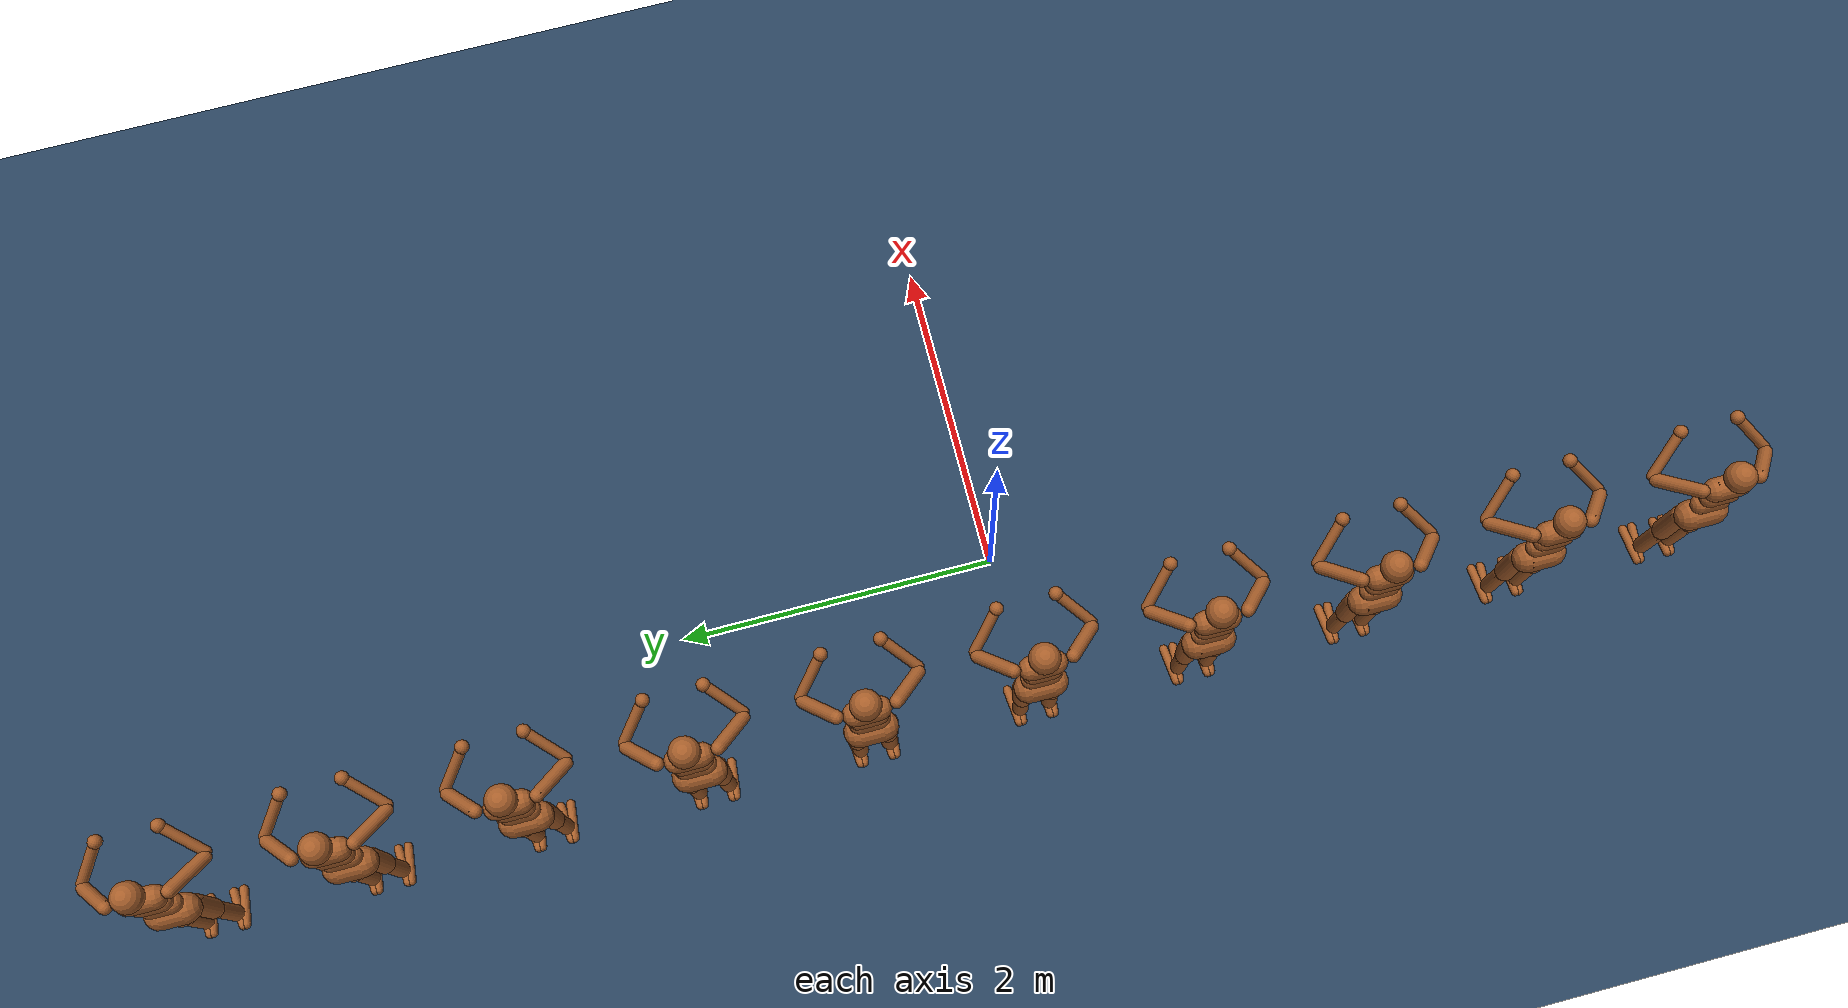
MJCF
<mujoco model="10 Humanoids">
  <compiler meshdir="F:/--CodeRepo/--CodeRepo/Research/___Mujoco/mujoco/mujoco/icse27/mujoco_rl_fuzz_2.0/.cache/repos/mjx/mjx/mujoco/mjx/test_data/humanoid" texturedir="F:/--CodeRepo/--CodeRepo/Research/___Mujoco/mujoco/mujoco/icse27/mujoco_rl_fuzz_2.0/.cache/repos/mjx/mjx/mujoco/mjx/test_data/humanoid" assetdir="F:/--CodeRepo/--CodeRepo/Research/___Mujoco/mujoco/mujoco/icse27/mujoco_rl_fuzz_2.0/.cache/repos/mjx/mjx/mujoco/mjx/test_data/humanoid"/><option timestep="0.005" solver="Newton" iterations="1" ls_iterations="4">
    <flag eulerdamp="disable"/>
  </option>

  <custom>
    <numeric data="40" name="max_contact_points"/>
    <numeric data="40" name="max_geom_pairs"/>
  </custom>

  <size memory="100M"/>

  <asset>
    <texture type="skybox" builtin="gradient" rgb1=".3 .5 .7" rgb2="0 0 0" width="512" height="512"/>
    <texture name="body" type="cube" builtin="flat" mark="cross" width="128" height="128" rgb1="0.8 0.6 0.4" rgb2="0.8 0.6 0.4" markrgb="1 1 1" random="0.01"/>
    <material name="body" texture="body" texuniform="true" rgba="0.8 0.6 .4 1"/>
    <texture name="grid" type="2d" builtin="checker" width="512" height="512" rgb1=".1 .2 .3" rgb2=".2 .3 .4"/>
    <material name="grid" texture="grid" texrepeat="1 1" texuniform="true" reflectance=".2"/>
  </asset>

  <default>
    <motor ctrlrange="-1 1" ctrllimited="true"/>
    <joint type="hinge" damping=".2" stiffness="1" armature=".01" limited="true" solimplimit="0 .99 .01"/>
    <default class="big_joint">
      <joint damping="5" stiffness="10"/>
      <default class="big_stiff_joint">
        <joint stiffness="20"/>
      </default>
    </default>
    <default class="body1">
      <geom type="capsule" condim="3" friction=".7" solimp=".9 .99 .003" solref=".015 1" material="body" contype="2" conaffinity="2045"/>
    </default>
    <default class="body2">
      <geom type="capsule" condim="3" friction=".7" solimp=".9 .99 .003" solref=".015 1" material="body" contype="4" conaffinity="2043"/>
    </default>
    <default class="body3">
      <geom type="capsule" condim="3" friction=".7" solimp=".9 .99 .003" solref=".015 1" material="body" contype="8" conaffinity="2039"/>
    </default>
    <default class="body4">
      <geom type="capsule" condim="3" friction=".7" solimp=".9 .99 .003" solref=".015 1" material="body" contype="16" conaffinity="2031"/>
    </default>
    <default class="body5">
      <geom type="capsule" condim="3" friction=".7" solimp=".9 .99 .003" solref=".015 1" material="body" contype="32" conaffinity="2015"/>
    </default>
    <default class="body6">
      <geom type="capsule" condim="3" friction=".7" solimp=".9 .99 .003" solref=".015 1" material="body" contype="64" conaffinity="1983"/>
    </default>
    <default class="body7">
      <geom type="capsule" condim="3" friction=".7" solimp=".9 .99 .003" solref=".015 1" material="body" contype="128" conaffinity="1919"/>
    </default>
    <default class="body8">
      <geom type="capsule" condim="3" friction=".7" solimp=".9 .99 .003" solref=".015 1" material="body" contype="256" conaffinity="1791"/>
    </default>
    <default class="body9">
      <geom type="capsule" condim="3" friction=".7" solimp=".9 .99 .003" solref=".015 1" material="body" contype="512" conaffinity="1535"/>
    </default>
    <default class="body10">
      <geom type="capsule" condim="3" friction=".7" solimp=".9 .99 .003" solref=".015 1" material="body" contype="1024" conaffinity="1023"/>
    </default>
  </default>

  <visual>
    <map force="0.1" zfar="30"/>
    <rgba haze="0.15 0.25 0.35 1"/>
    <quality shadowsize="4096"/>
    <global offwidth="800" offheight="800"/>
  </visual>

  <worldbody>
    <geom size="10 10 .05" type="plane" material="grid" condim="3"/>
    <light dir=".2 1 -.4" diffuse=".8 .8 .8" specular="0.3 0.3 0.3" pos="-2 -10 4" cutoff="35"/>
    <light dir="-.2 1 -.4" diffuse=".8 .8 .8" specular="0.3 0.3 0.3" pos="2 -10 4" cutoff="35"/>

    <body name="1a_torso" pos="-1 0 1.5" childclass="body1">
      <camera name="1a_back" pos="-3 0 1" xyaxes="0 -1 0 1 0 2" mode="trackcom"/>
      <camera name="1a_side" pos="0 -3 1" xyaxes="1 0 0 0 1 2" mode="trackcom"/>
      <freejoint name="1a_root"/>
      <geom name="1a_torso" fromto="0 -.07 0 0 .07 0" size=".07"/>
      <geom name="1a_upper_waist" fromto="-.01 -.06 -.12 -.01 .06 -.12" size=".06"/>
      <body name="1a_head" pos="0 0 .19">
        <geom name="1a_head" type="sphere" size=".09"/>
        <camera name="1a_egocentric" pos=".09 0 0" xyaxes="0 -1 0 .1 0 1" fovy="80"/>
      </body>
      <body name="1a_lower_waist" pos="-.01 0 -.26">
        <geom name="1a_lower_waist" fromto="0 -.06 0 0 .06 0" size=".06"/>
        <joint name="1a_abdomen_z" pos="0 0 .065" axis="0 0 1" range="-45 45" class="big_stiff_joint"/>
        <joint name="1a_abdomen_y" pos="0 0 .065" axis="0 1 0" range="-75 30" class="big_joint"/>
        <body name="1a_pelvis" pos="0 0 -.165">
          <joint name="1a_abdomen_x" pos="0 0 .1" axis="1 0 0" range="-35 35" class="big_joint"/>
          <geom name="1a_butt" fromto="-.02 -.07 0 -.02 .07 0" size=".09"/>
          <body name="1a_right_thigh" pos="0 -.1 -.04">
            <joint name="1a_right_hip_x" axis="1 0 0" range="-25 5" class="big_joint"/>
            <joint name="1a_right_hip_z" axis="0 0 1" range="-60 35" class="big_joint"/>
            <joint name="1a_right_hip_y" axis="0 1 0" range="-110 20" class="big_stiff_joint"/>
            <geom name="1a_right_thigh" fromto="0 0 0 0 .01 -.34" size=".06"/>
            <body name="1a_right_shin" pos="0 .01 -.403">
              <joint name="1a_right_knee" pos="0 0 .02" axis="0 -1 0" range="-160 2"/>
              <geom name="1a_right_shin" fromto="0 0 0 0 0 -.3" size=".049"/>
              <body name="1a_right_foot" pos="0 0 -.39">
                <joint name="1a_right_ankle_y" pos="0 0 .08" axis="0 1 0" range="-50 50" stiffness="6"/>
                <joint name="1a_right_ankle_x" pos="0 0 .04" axis="1 0 .5" range="-50 50" stiffness="3"/>
                <geom name="1a_right_right_foot" fromto="-.07 -.02 0 .14 -.04 0" size=".027"/>
                <geom name="1a_left_right_foot" fromto="-.07 0 0 .14  .02 0" size=".027"/>
              </body>
            </body>
          </body>
          <body name="1a_left_thigh" pos="0 .1 -.04">
            <joint name="1a_left_hip_x" axis="-1 0 0" range="-25 5" class="big_joint"/>
            <joint name="1a_left_hip_z" axis="0 0 -1" range="-60 35" class="big_joint"/>
            <joint name="1a_left_hip_y" axis="0 1 0" range="-110 20" class="big_stiff_joint"/>
            <geom name="1a_left_thigh" fromto="0 0 0 0 -.01 -.34" size=".06"/>
            <body name="1a_left_shin" pos="0 -.01 -.403">
              <joint name="1a_left_knee" pos="0 0 .02" axis="0 -1 0" range="-160 2"/>
              <geom name="1a_left_shin" fromto="0 0 0 0 0 -.3" size=".049"/>
              <body name="1a_left_foot" pos="0 0 -.39">
                <joint name="1a_left_ankle_y" pos="0 0 .08" axis="0 1 0" range="-50 50" stiffness="6"/>
                <joint name="1a_left_ankle_x" pos="0 0 .04" axis="1 0 .5" range="-50 50" stiffness="3"/>
                <geom name="1a_left_left_foot" fromto="-.07 .02 0 .14 .04 0" size=".027"/>
                <geom name="1a_right_left_foot" fromto="-.07 0 0 .14 -.02 0" size=".027"/>
              </body>
            </body>
          </body>
        </body>
      </body>
      <body name="1a_right_upper_arm" pos="0 -.17 .06">
        <joint name="1a_right_shoulder1" axis="2 1 1" range="-85 60"/>
        <joint name="1a_right_shoulder2" axis="0 -1 1" range="-85 60"/>
        <geom name="1a_right_upper_arm" fromto="0 0 0 .16 -.16 -.16" size=".04 .16"/>
        <body name="1a_right_lower_arm" pos=".18 -.18 -.18">
          <joint name="1a_right_elbow" axis="0 -1 1" range="-90 50" stiffness="0"/>
          <geom name="1a_right_lower_arm" fromto=".01 .01 .01 .17 .17 .17" size=".031"/>
          <body name="1a_right_hand" pos=".18 .18 .18">
            <geom name="1a_right_hand" type="sphere" size=".04" zaxis="1 1 1"/>
          </body>
        </body>
      </body>
      <body name="1a_left_upper_arm" pos="0 .17 .06">
        <joint name="1a_left_shoulder1" axis="2 -1 1" range="-60 85"/>
        <joint name="1a_left_shoulder2" axis="0 1 1" range="-60 85"/>
        <geom name="1a_left_upper_arm" fromto="0 0 0 .16 .16 -.16" size=".04 .16"/>
        <body name="1a_left_lower_arm" pos=".18 .18 -.18">
          <joint name="1a_left_elbow" axis="0 -1 -1" range="-90 50" stiffness="0"/>
          <geom name="1a_left_lower_arm" fromto=".01 -.01 .01 .17 -.17 .17" size=".031"/>
          <body name="1a_left_hand" pos=".18 -.18 .18">
            <geom name="1a_left_hand" type="sphere" size=".04" zaxis="1 -1 1"/>
          </body>
        </body>
      </body>
    </body>

    <body name="2a_torso" pos="-1 1 1.5" childclass="body2">
      <camera name="2a_back" pos="-3 0 1" xyaxes="0 -1 0 1 0 2" mode="trackcom"/>
      <camera name="2a_side" pos="0 -3 1" xyaxes="1 0 0 0 1 2" mode="trackcom"/>
      <freejoint name="2a_root"/>
      <geom name="2a_torso" fromto="0 -.07 0 0 .07 0" size=".07"/>
      <geom name="2a_upper_waist" fromto="-.01 -.06 -.12 -.01 .06 -.12" size=".06"/>
      <body name="2a_head" pos="0 0 .19">
        <geom name="2a_head" type="sphere" size=".09"/>
        <camera name="2a_egocentric" pos=".09 0 0" xyaxes="0 -1 0 .1 0 1" fovy="80"/>
      </body>
      <body name="2a_lower_waist" pos="-.01 0 -.26">
        <geom name="2a_lower_waist" fromto="0 -.06 0 0 .06 0" size=".06"/>
        <joint name="2a_abdomen_z" pos="0 0 .065" axis="0 0 1" range="-45 45" class="big_stiff_joint"/>
        <joint name="2a_abdomen_y" pos="0 0 .065" axis="0 1 0" range="-75 30" class="big_joint"/>
        <body name="2a_pelvis" pos="0 0 -.165">
          <joint name="2a_abdomen_x" pos="0 0 .1" axis="1 0 0" range="-35 35" class="big_joint"/>
          <geom name="2a_butt" fromto="-.02 -.07 0 -.02 .07 0" size=".09"/>
          <body name="2a_right_thigh" pos="0 -.1 -.04">
            <joint name="2a_right_hip_x" axis="1 0 0" range="-25 5" class="big_joint"/>
            <joint name="2a_right_hip_z" axis="0 0 1" range="-60 35" class="big_joint"/>
            <joint name="2a_right_hip_y" axis="0 1 0" range="-110 20" class="big_stiff_joint"/>
            <geom name="2a_right_thigh" fromto="0 0 0 0 .01 -.34" size=".06"/>
            <body name="2a_right_shin" pos="0 .01 -.403">
              <joint name="2a_right_knee" pos="0 0 .02" axis="0 -1 0" range="-160 2"/>
              <geom name="2a_right_shin" fromto="0 0 0 0 0 -.3" size=".049"/>
              <body name="2a_right_foot" pos="0 0 -.39">
                <joint name="2a_right_ankle_y" pos="0 0 .08" axis="0 1 0" range="-50 50" stiffness="6"/>
                <joint name="2a_right_ankle_x" pos="0 0 .04" axis="1 0 .5" range="-50 50" stiffness="3"/>
                <geom name="2a_right_right_foot" fromto="-.07 -.02 0 .14 -.04 0" size=".027"/>
                <geom name="2a_left_right_foot" fromto="-.07 0 0 .14  .02 0" size=".027"/>
              </body>
            </body>
          </body>
          <body name="2a_left_thigh" pos="0 .1 -.04">
            <joint name="2a_left_hip_x" axis="-1 0 0" range="-25 5" class="big_joint"/>
            <joint name="2a_left_hip_z" axis="0 0 -1" range="-60 35" class="big_joint"/>
            <joint name="2a_left_hip_y" axis="0 1 0" range="-110 20" class="big_stiff_joint"/>
            <geom name="2a_left_thigh" fromto="0 0 0 0 -.01 -.34" size=".06"/>
            <body name="2a_left_shin" pos="0 -.01 -.403">
              <joint name="2a_left_knee" pos="0 0 .02" axis="0 -1 0" range="-160 2"/>
              <geom name="2a_left_shin" fromto="0 0 0 0 0 -.3" size=".049"/>
              <body name="2a_left_foot" pos="0 0 -.39">
                <joint name="2a_left_ankle_y" pos="0 0 .08" axis="0 1 0" range="-50 50" stiffness="6"/>
                <joint name="2a_left_ankle_x" pos="0 0 .04" axis="1 0 .5" range="-50 50" stiffness="3"/>
                <geom name="2a_left_left_foot" fromto="-.07 .02 0 .14 .04 0" size=".027"/>
                <geom name="2a_right_left_foot" fromto="-.07 0 0 .14 -.02 0" size=".027"/>
              </body>
            </body>
          </body>
        </body>
      </body>
      <body name="2a_right_upper_arm" pos="0 -.17 .06">
        <joint name="2a_right_shoulder1" axis="2 1 1" range="-85 60"/>
        <joint name="2a_right_shoulder2" axis="0 -1 1" range="-85 60"/>
        <geom name="2a_right_upper_arm" fromto="0 0 0 .16 -.16 -.16" size=".04 .16"/>
        <body name="2a_right_lower_arm" pos=".18 -.18 -.18">
          <joint name="2a_right_elbow" axis="0 -1 1" range="-90 50" stiffness="0"/>
          <geom name="2a_right_lower_arm" fromto=".01 .01 .01 .17 .17 .17" size=".031"/>
          <body name="2a_right_hand" pos=".18 .18 .18">
            <geom name="2a_right_hand" type="sphere" size=".04" zaxis="1 1 1"/>
          </body>
        </body>
      </body>
      <body name="2a_left_upper_arm" pos="0 .17 .06">
        <joint name="2a_left_shoulder1" axis="2 -1 1" range="-60 85"/>
        <joint name="2a_left_shoulder2" axis="0 1 1" range="-60 85"/>
        <geom name="2a_left_upper_arm" fromto="0 0 0 .16 .16 -.16" size=".04 .16"/>
        <body name="2a_left_lower_arm" pos=".18 .18 -.18">
          <joint name="2a_left_elbow" axis="0 -1 -1" range="-90 50" stiffness="0"/>
          <geom name="2a_left_lower_arm" fromto=".01 -.01 .01 .17 -.17 .17" size=".031"/>
          <body name="2a_left_hand" pos=".18 -.18 .18">
            <geom name="2a_left_hand" type="sphere" size=".04" zaxis="1 -1 1"/>
          </body>
        </body>
      </body>
    </body>

    <body name="3a_torso" pos="-1 -1 1.5" childclass="body3">
      <camera name="3a_back" pos="-3 0 1" xyaxes="0 -1 0 1 0 2" mode="trackcom"/>
      <camera name="3a_side" pos="0 -3 1" xyaxes="1 0 0 0 1 2" mode="trackcom"/>
      <freejoint name="3a_root"/>
      <geom name="3a_torso" fromto="0 -.07 0 0 .07 0" size=".07"/>
      <geom name="3a_upper_waist" fromto="-.01 -.06 -.12 -.01 .06 -.12" size=".06"/>
      <body name="3a_head" pos="0 0 .19">
        <geom name="3a_head" type="sphere" size=".09"/>
        <camera name="3a_egocentric" pos=".09 0 0" xyaxes="0 -1 0 .1 0 1" fovy="80"/>
      </body>
      <body name="3a_lower_waist" pos="-.01 0 -.26">
        <geom name="3a_lower_waist" fromto="0 -.06 0 0 .06 0" size=".06"/>
        <joint name="3a_abdomen_z" pos="0 0 .065" axis="0 0 1" range="-45 45" class="big_stiff_joint"/>
        <joint name="3a_abdomen_y" pos="0 0 .065" axis="0 1 0" range="-75 30" class="big_joint"/>
        <body name="3a_pelvis" pos="0 0 -.165">
          <joint name="3a_abdomen_x" pos="0 0 .1" axis="1 0 0" range="-35 35" class="big_joint"/>
          <geom name="3a_butt" fromto="-.02 -.07 0 -.02 .07 0" size=".09"/>
          <body name="3a_right_thigh" pos="0 -.1 -.04">
            <joint name="3a_right_hip_x" axis="1 0 0" range="-25 5" class="big_joint"/>
            <joint name="3a_right_hip_z" axis="0 0 1" range="-60 35" class="big_joint"/>
            <joint name="3a_right_hip_y" axis="0 1 0" range="-110 20" class="big_stiff_joint"/>
            <geom name="3a_right_thigh" fromto="0 0 0 0 .01 -.34" size=".06"/>
            <body name="3a_right_shin" pos="0 .01 -.403">
              <joint name="3a_right_knee" pos="0 0 .02" axis="0 -1 0" range="-160 2"/>
              <geom name="3a_right_shin" fromto="0 0 0 0 0 -.3" size=".049"/>
              <body name="3a_right_foot" pos="0 0 -.39">
                <joint name="3a_right_ankle_y" pos="0 0 .08" axis="0 1 0" range="-50 50" stiffness="6"/>
                <joint name="3a_right_ankle_x" pos="0 0 .04" axis="1 0 .5" range="-50 50" stiffness="3"/>
                <geom name="3a_right_right_foot" fromto="-.07 -.02 0 .14 -.04 0" size=".027"/>
                <geom name="3a_left_right_foot" fromto="-.07 0 0 .14  .02 0" size=".027"/>
              </body>
            </body>
          </body>
          <body name="3a_left_thigh" pos="0 .1 -.04">
            <joint name="3a_left_hip_x" axis="-1 0 0" range="-25 5" class="big_joint"/>
            <joint name="3a_left_hip_z" axis="0 0 -1" range="-60 35" class="big_joint"/>
            <joint name="3a_left_hip_y" axis="0 1 0" range="-110 20" class="big_stiff_joint"/>
            <geom name="3a_left_thigh" fromto="0 0 0 0 -.01 -.34" size=".06"/>
            <body name="3a_left_shin" pos="0 -.01 -.403">
              <joint name="3a_left_knee" pos="0 0 .02" axis="0 -1 0" range="-160 2"/>
              <geom name="3a_left_shin" fromto="0 0 0 0 0 -.3" size=".049"/>
              <body name="3a_left_foot" pos="0 0 -.39">
                <joint name="3a_left_ankle_y" pos="0 0 .08" axis="0 1 0" range="-50 50" stiffness="6"/>
                <joint name="3a_left_ankle_x" pos="0 0 .04" axis="1 0 .5" range="-50 50" stiffness="3"/>
                <geom name="3a_left_left_foot" fromto="-.07 .02 0 .14 .04 0" size=".027"/>
                <geom name="3a_right_left_foot" fromto="-.07 0 0 .14 -.02 0" size=".027"/>
              </body>
            </body>
          </body>
        </body>
      </body>
      <body name="3a_right_upper_arm" pos="0 -.17 .06">
        <joint name="3a_right_shoulder1" axis="2 1 1" range="-85 60"/>
        <joint name="3a_right_shoulder2" axis="0 -1 1" range="-85 60"/>
        <geom name="3a_right_upper_arm" fromto="0 0 0 .16 -.16 -.16" size=".04 .16"/>
        <body name="3a_right_lower_arm" pos=".18 -.18 -.18">
          <joint name="3a_right_elbow" axis="0 -1 1" range="-90 50" stiffness="0"/>
          <geom name="3a_right_lower_arm" fromto=".01 .01 .01 .17 .17 .17" size=".031"/>
          <body name="3a_right_hand" pos=".18 .18 .18">
            <geom name="3a_right_hand" type="sphere" size=".04" zaxis="1 1 1"/>
          </body>
        </body>
      </body>
      <body name="3a_left_upper_arm" pos="0 .17 .06">
        <joint name="3a_left_shoulder1" axis="2 -1 1" range="-60 85"/>
        <joint name="3a_left_shoulder2" axis="0 1 1" range="-60 85"/>
        <geom name="3a_left_upper_arm" fromto="0 0 0 .16 .16 -.16" size=".04 .16"/>
        <body name="3a_left_lower_arm" pos=".18 .18 -.18">
          <joint name="3a_left_elbow" axis="0 -1 -1" range="-90 50" stiffness="0"/>
          <geom name="3a_left_lower_arm" fromto=".01 -.01 .01 .17 -.17 .17" size=".031"/>
          <body name="3a_left_hand" pos=".18 -.18 .18">
            <geom name="3a_left_hand" type="sphere" size=".04" zaxis="1 -1 1"/>
          </body>
        </body>
      </body>
    </body>

    <body name="4a_torso" pos="-1 2 1.5" childclass="body4">
      <camera name="4a_back" pos="-3 0 1" xyaxes="0 -1 0 1 0 2" mode="trackcom"/>
      <camera name="4a_side" pos="0 -3 1" xyaxes="1 0 0 0 1 2" mode="trackcom"/>
      <freejoint name="4a_root"/>
      <geom name="4a_torso" fromto="0 -.07 0 0 .07 0" size=".07"/>
      <geom name="4a_upper_waist" fromto="-.01 -.06 -.12 -.01 .06 -.12" size=".06"/>
      <body name="4a_head" pos="0 0 .19">
        <geom name="4a_head" type="sphere" size=".09"/>
        <camera name="4a_egocentric" pos=".09 0 0" xyaxes="0 -1 0 .1 0 1" fovy="80"/>
      </body>
      <body name="4a_lower_waist" pos="-.01 0 -.26">
        <geom name="4a_lower_waist" fromto="0 -.06 0 0 .06 0" size=".06"/>
        <joint name="4a_abdomen_z" pos="0 0 .065" axis="0 0 1" range="-45 45" class="big_stiff_joint"/>
        <joint name="4a_abdomen_y" pos="0 0 .065" axis="0 1 0" range="-75 30" class="big_joint"/>
        <body name="4a_pelvis" pos="0 0 -.165">
          <joint name="4a_abdomen_x" pos="0 0 .1" axis="1 0 0" range="-35 35" class="big_joint"/>
          <geom name="4a_butt" fromto="-.02 -.07 0 -.02 .07 0" size=".09"/>
          <body name="4a_right_thigh" pos="0 -.1 -.04">
            <joint name="4a_right_hip_x" axis="1 0 0" range="-25 5" class="big_joint"/>
            <joint name="4a_right_hip_z" axis="0 0 1" range="-60 35" class="big_joint"/>
            <joint name="4a_right_hip_y" axis="0 1 0" range="-110 20" class="big_stiff_joint"/>
            <geom name="4a_right_thigh" fromto="0 0 0 0 .01 -.34" size=".06"/>
            <body name="4a_right_shin" pos="0 .01 -.403">
              <joint name="4a_right_knee" pos="0 0 .02" axis="0 -1 0" range="-160 2"/>
              <geom name="4a_right_shin" fromto="0 0 0 0 0 -.3" size=".049"/>
              <body name="4a_right_foot" pos="0 0 -.39">
                <joint name="4a_right_ankle_y" pos="0 0 .08" axis="0 1 0" range="-50 50" stiffness="6"/>
                <joint name="4a_right_ankle_x" pos="0 0 .04" axis="1 0 .5" range="-50 50" stiffness="3"/>
                <geom name="4a_right_right_foot" fromto="-.07 -.02 0 .14 -.04 0" size=".027"/>
                <geom name="4a_left_right_foot" fromto="-.07 0 0 .14  .02 0" size=".027"/>
              </body>
            </body>
          </body>
          <body name="4a_left_thigh" pos="0 .1 -.04">
            <joint name="4a_left_hip_x" axis="-1 0 0" range="-25 5" class="big_joint"/>
            <joint name="4a_left_hip_z" axis="0 0 -1" range="-60 35" class="big_joint"/>
            <joint name="4a_left_hip_y" axis="0 1 0" range="-110 20" class="big_stiff_joint"/>
            <geom name="4a_left_thigh" fromto="0 0 0 0 -.01 -.34" size=".06"/>
            <body name="4a_left_shin" pos="0 -.01 -.403">
              <joint name="4a_left_knee" pos="0 0 .02" axis="0 -1 0" range="-160 2"/>
              <geom name="4a_left_shin" fromto="0 0 0 0 0 -.3" size=".049"/>
              <body name="4a_left_foot" pos="0 0 -.39">
                <joint name="4a_left_ankle_y" pos="0 0 .08" axis="0 1 0" range="-50 50" stiffness="6"/>
                <joint name="4a_left_ankle_x" pos="0 0 .04" axis="1 0 .5" range="-50 50" stiffness="3"/>
                <geom name="4a_left_left_foot" fromto="-.07 .02 0 .14 .04 0" size=".027"/>
                <geom name="4a_right_left_foot" fromto="-.07 0 0 .14 -.02 0" size=".027"/>
              </body>
            </body>
          </body>
        </body>
      </body>
      <body name="4a_right_upper_arm" pos="0 -.17 .06">
        <joint name="4a_right_shoulder1" axis="2 1 1" range="-85 60"/>
        <joint name="4a_right_shoulder2" axis="0 -1 1" range="-85 60"/>
        <geom name="4a_right_upper_arm" fromto="0 0 0 .16 -.16 -.16" size=".04 .16"/>
        <body name="4a_right_lower_arm" pos=".18 -.18 -.18">
          <joint name="4a_right_elbow" axis="0 -1 1" range="-90 50" stiffness="0"/>
          <geom name="4a_right_lower_arm" fromto=".01 .01 .01 .17 .17 .17" size=".031"/>
          <body name="4a_right_hand" pos=".18 .18 .18">
            <geom name="4a_right_hand" type="sphere" size=".04" zaxis="1 1 1"/>
          </body>
        </body>
      </body>
      <body name="4a_left_upper_arm" pos="0 .17 .06">
        <joint name="4a_left_shoulder1" axis="2 -1 1" range="-60 85"/>
        <joint name="4a_left_shoulder2" axis="0 1 1" range="-60 85"/>
        <geom name="4a_left_upper_arm" fromto="0 0 0 .16 .16 -.16" size=".04 .16"/>
        <body name="4a_left_lower_arm" pos=".18 .18 -.18">
          <joint name="4a_left_elbow" axis="0 -1 -1" range="-90 50" stiffness="0"/>
          <geom name="4a_left_lower_arm" fromto=".01 -.01 .01 .17 -.17 .17" size=".031"/>
          <body name="4a_left_hand" pos=".18 -.18 .18">
            <geom name="4a_left_hand" type="sphere" size=".04" zaxis="1 -1 1"/>
          </body>
        </body>
      </body>
    </body>

    <body name="5a_torso" pos="-1 -2 1.5" childclass="body5">
      <camera name="5a_back" pos="-3 0 1" xyaxes="0 -1 0 1 0 2" mode="trackcom"/>
      <camera name="5a_side" pos="0 -3 1" xyaxes="1 0 0 0 1 2" mode="trackcom"/>
      <freejoint name="5a_root"/>
      <geom name="5a_torso" fromto="0 -.07 0 0 .07 0" size=".07"/>
      <geom name="5a_upper_waist" fromto="-.01 -.06 -.12 -.01 .06 -.12" size=".06"/>
      <body name="5a_head" pos="0 0 .19">
        <geom name="5a_head" type="sphere" size=".09"/>
        <camera name="5a_egocentric" pos=".09 0 0" xyaxes="0 -1 0 .1 0 1" fovy="80"/>
      </body>
      <body name="5a_lower_waist" pos="-.01 0 -.26">
        <geom name="5a_lower_waist" fromto="0 -.06 0 0 .06 0" size=".06"/>
        <joint name="5a_abdomen_z" pos="0 0 .065" axis="0 0 1" range="-45 45" class="big_stiff_joint"/>
        <joint name="5a_abdomen_y" pos="0 0 .065" axis="0 1 0" range="-75 30" class="big_joint"/>
        <body name="5a_pelvis" pos="0 0 -.165">
          <joint name="5a_abdomen_x" pos="0 0 .1" axis="1 0 0" range="-35 35" class="big_joint"/>
          <geom name="5a_butt" fromto="-.02 -.07 0 -.02 .07 0" size=".09"/>
          <body name="5a_right_thigh" pos="0 -.1 -.04">
            <joint name="5a_right_hip_x" axis="1 0 0" range="-25 5" class="big_joint"/>
            <joint name="5a_right_hip_z" axis="0 0 1" range="-60 35" class="big_joint"/>
            <joint name="5a_right_hip_y" axis="0 1 0" range="-110 20" class="big_stiff_joint"/>
            <geom name="5a_right_thigh" fromto="0 0 0 0 .01 -.34" size=".06"/>
            <body name="5a_right_shin" pos="0 .01 -.403">
              <joint name="5a_right_knee" pos="0 0 .02" axis="0 -1 0" range="-160 2"/>
              <geom name="5a_right_shin" fromto="0 0 0 0 0 -.3" size=".049"/>
              <body name="5a_right_foot" pos="0 0 -.39">
                <joint name="5a_right_ankle_y" pos="0 0 .08" axis="0 1 0" range="-50 50" stiffness="6"/>
                <joint name="5a_right_ankle_x" pos="0 0 .04" axis="1 0 .5" range="-50 50" stiffness="3"/>
                <geom name="5a_right_right_foot" fromto="-.07 -.02 0 .14 -.04 0" size=".027"/>
                <geom name="5a_left_right_foot" fromto="-.07 0 0 .14  .02 0" size=".027"/>
              </body>
            </body>
          </body>
          <body name="5a_left_thigh" pos="0 .1 -.04">
            <joint name="5a_left_hip_x" axis="-1 0 0" range="-25 5" class="big_joint"/>
            <joint name="5a_left_hip_z" axis="0 0 -1" range="-60 35" class="big_joint"/>
            <joint name="5a_left_hip_y" axis="0 1 0" range="-110 20" class="big_stiff_joint"/>
            <geom name="5a_left_thigh" fromto="0 0 0 0 -.01 -.34" size=".06"/>
            <body name="5a_left_shin" pos="0 -.01 -.403">
              <joint name="5a_left_knee" pos="0 0 .02" axis="0 -1 0" range="-160 2"/>
              <geom name="5a_left_shin" fromto="0 0 0 0 0 -.3" size=".049"/>
              <body name="5a_left_foot" pos="0 0 -.39">
                <joint name="5a_left_ankle_y" pos="0 0 .08" axis="0 1 0" range="-50 50" stiffness="6"/>
                <joint name="5a_left_ankle_x" pos="0 0 .04" axis="1 0 .5" range="-50 50" stiffness="3"/>
                <geom name="5a_left_left_foot" fromto="-.07 .02 0 .14 .04 0" size=".027"/>
                <geom name="5a_right_left_foot" fromto="-.07 0 0 .14 -.02 0" size=".027"/>
              </body>
            </body>
          </body>
        </body>
      </body>
      <body name="5a_right_upper_arm" pos="0 -.17 .06">
        <joint name="5a_right_shoulder1" axis="2 1 1" range="-85 60"/>
        <joint name="5a_right_shoulder2" axis="0 -1 1" range="-85 60"/>
        <geom name="5a_right_upper_arm" fromto="0 0 0 .16 -.16 -.16" size=".04 .16"/>
        <body name="5a_right_lower_arm" pos=".18 -.18 -.18">
          <joint name="5a_right_elbow" axis="0 -1 1" range="-90 50" stiffness="0"/>
          <geom name="5a_right_lower_arm" fromto=".01 .01 .01 .17 .17 .17" size=".031"/>
          <body name="5a_right_hand" pos=".18 .18 .18">
            <geom name="5a_right_hand" type="sphere" size=".04" zaxis="1 1 1"/>
          </body>
        </body>
      </body>
      <body name="5a_left_upper_arm" pos="0 .17 .06">
        <joint name="5a_left_shoulder1" axis="2 -1 1" range="-60 85"/>
        <joint name="5a_left_shoulder2" axis="0 1 1" range="-60 85"/>
        <geom name="5a_left_upper_arm" fromto="0 0 0 .16 .16 -.16" size=".04 .16"/>
        <body name="5a_left_lower_arm" pos=".18 .18 -.18">
          <joint name="5a_left_elbow" axis="0 -1 -1" range="-90 50" stiffness="0"/>
          <geom name="5a_left_lower_arm" fromto=".01 -.01 .01 .17 -.17 .17" size=".031"/>
          <body name="5a_left_hand" pos=".18 -.18 .18">
            <geom name="5a_left_hand" type="sphere" size=".04" zaxis="1 -1 1"/>
          </body>
        </body>
      </body>
    </body>

    <body name="6a_torso" pos="-1 3 1.5" childclass="body6">
      <camera name="6a_back" pos="-3 0 1" xyaxes="0 -1 0 1 0 2" mode="trackcom"/>
      <camera name="6a_side" pos="0 -3 1" xyaxes="1 0 0 0 1 2" mode="trackcom"/>
      <freejoint name="6a_root"/>
      <geom name="6a_torso" fromto="0 -.07 0 0 .07 0" size=".07"/>
      <geom name="6a_upper_waist" fromto="-.01 -.06 -.12 -.01 .06 -.12" size=".06"/>
      <body name="6a_head" pos="0 0 .19">
        <geom name="6a_head" type="sphere" size=".09"/>
        <camera name="6a_egocentric" pos=".09 0 0" xyaxes="0 -1 0 .1 0 1" fovy="80"/>
      </body>
      <body name="6a_lower_waist" pos="-.01 0 -.26">
        <geom name="6a_lower_waist" fromto="0 -.06 0 0 .06 0" size=".06"/>
        <joint name="6a_abdomen_z" pos="0 0 .065" axis="0 0 1" range="-45 45" class="big_stiff_joint"/>
        <joint name="6a_abdomen_y" pos="0 0 .065" axis="0 1 0" range="-75 30" class="big_joint"/>
        <body name="6a_pelvis" pos="0 0 -.165">
          <joint name="6a_abdomen_x" pos="0 0 .1" axis="1 0 0" range="-35 35" class="big_joint"/>
          <geom name="6a_butt" fromto="-.02 -.07 0 -.02 .07 0" size=".09"/>
          <body name="6a_right_thigh" pos="0 -.1 -.04">
            <joint name="6a_right_hip_x" axis="1 0 0" range="-25 5" class="big_joint"/>
            <joint name="6a_right_hip_z" axis="0 0 1" range="-60 35" class="big_joint"/>
            <joint name="6a_right_hip_y" axis="0 1 0" range="-110 20" class="big_stiff_joint"/>
            <geom name="6a_right_thigh" fromto="0 0 0 0 .01 -.34" size=".06"/>
            <body name="6a_right_shin" pos="0 .01 -.403">
              <joint name="6a_right_knee" pos="0 0 .02" axis="0 -1 0" range="-160 2"/>
              <geom name="6a_right_shin" fromto="0 0 0 0 0 -.3" size=".049"/>
              <body name="6a_right_foot" pos="0 0 -.39">
                <joint name="6a_right_ankle_y" pos="0 0 .08" axis="0 1 0" range="-50 50" stiffness="6"/>
                <joint name="6a_right_ankle_x" pos="0 0 .04" axis="1 0 .5" range="-50 50" stiffness="3"/>
                <geom name="6a_right_right_foot" fromto="-.07 -.02 0 .14 -.04 0" size=".027"/>
                <geom name="6a_left_right_foot" fromto="-.07 0 0 .14  .02 0" size=".027"/>
              </body>
            </body>
          </body>
          <body name="6a_left_thigh" pos="0 .1 -.04">
            <joint name="6a_left_hip_x" axis="-1 0 0" range="-25 5" class="big_joint"/>
            <joint name="6a_left_hip_z" axis="0 0 -1" range="-60 35" class="big_joint"/>
            <joint name="6a_left_hip_y" axis="0 1 0" range="-110 20" class="big_stiff_joint"/>
            <geom name="6a_left_thigh" fromto="0 0 0 0 -.01 -.34" size=".06"/>
            <body name="6a_left_shin" pos="0 -.01 -.403">
              <joint name="6a_left_knee" pos="0 0 .02" axis="0 -1 0" range="-160 2"/>
              <geom name="6a_left_shin" fromto="0 0 0 0 0 -.3" size=".049"/>
              <body name="6a_left_foot" pos="0 0 -.39">
                <joint name="6a_left_ankle_y" pos="0 0 .08" axis="0 1 0" range="-50 50" stiffness="6"/>
                <joint name="6a_left_ankle_x" pos="0 0 .04" axis="1 0 .5" range="-50 50" stiffness="3"/>
                <geom name="6a_left_left_foot" fromto="-.07 .02 0 .14 .04 0" size=".027"/>
                <geom name="6a_right_left_foot" fromto="-.07 0 0 .14 -.02 0" size=".027"/>
              </body>
            </body>
          </body>
        </body>
      </body>
      <body name="6a_right_upper_arm" pos="0 -.17 .06">
        <joint name="6a_right_shoulder1" axis="2 1 1" range="-85 60"/>
        <joint name="6a_right_shoulder2" axis="0 -1 1" range="-85 60"/>
        <geom name="6a_right_upper_arm" fromto="0 0 0 .16 -.16 -.16" size=".04 .16"/>
        <body name="6a_right_lower_arm" pos=".18 -.18 -.18">
          <joint name="6a_right_elbow" axis="0 -1 1" range="-90 50" stiffness="0"/>
          <geom name="6a_right_lower_arm" fromto=".01 .01 .01 .17 .17 .17" size=".031"/>
          <body name="6a_right_hand" pos=".18 .18 .18">
            <geom name="6a_right_hand" type="sphere" size=".04" zaxis="1 1 1"/>
          </body>
        </body>
      </body>
      <body name="6a_left_upper_arm" pos="0 .17 .06">
        <joint name="6a_left_shoulder1" axis="2 -1 1" range="-60 85"/>
        <joint name="6a_left_shoulder2" axis="0 1 1" range="-60 85"/>
        <geom name="6a_left_upper_arm" fromto="0 0 0 .16 .16 -.16" size=".04 .16"/>
        <body name="6a_left_lower_arm" pos=".18 .18 -.18">
          <joint name="6a_left_elbow" axis="0 -1 -1" range="-90 50" stiffness="0"/>
          <geom name="6a_left_lower_arm" fromto=".01 -.01 .01 .17 -.17 .17" size=".031"/>
          <body name="6a_left_hand" pos=".18 -.18 .18">
            <geom name="6a_left_hand" type="sphere" size=".04" zaxis="1 -1 1"/>
          </body>
        </body>
      </body>
    </body>

    <body name="7a_torso" pos="-1 -3 1.5" childclass="body7">
      <camera name="7a_back" pos="-3 0 1" xyaxes="0 -1 0 1 0 2" mode="trackcom"/>
      <camera name="7a_side" pos="0 -3 1" xyaxes="1 0 0 0 1 2" mode="trackcom"/>
      <freejoint name="7a_root"/>
      <geom name="7a_torso" fromto="0 -.07 0 0 .07 0" size=".07"/>
      <geom name="7a_upper_waist" fromto="-.01 -.06 -.12 -.01 .06 -.12" size=".06"/>
      <body name="7a_head" pos="0 0 .19">
        <geom name="7a_head" type="sphere" size=".09"/>
        <camera name="7a_egocentric" pos=".09 0 0" xyaxes="0 -1 0 .1 0 1" fovy="80"/>
      </body>
      <body name="7a_lower_waist" pos="-.01 0 -.26">
        <geom name="7a_lower_waist" fromto="0 -.06 0 0 .06 0" size=".06"/>
        <joint name="7a_abdomen_z" pos="0 0 .065" axis="0 0 1" range="-45 45" class="big_stiff_joint"/>
        <joint name="7a_abdomen_y" pos="0 0 .065" axis="0 1 0" range="-75 30" class="big_joint"/>
        <body name="7a_pelvis" pos="0 0 -.165">
          <joint name="7a_abdomen_x" pos="0 0 .1" axis="1 0 0" range="-35 35" class="big_joint"/>
          <geom name="7a_butt" fromto="-.02 -.07 0 -.02 .07 0" size=".09"/>
          <body name="7a_right_thigh" pos="0 -.1 -.04">
            <joint name="7a_right_hip_x" axis="1 0 0" range="-25 5" class="big_joint"/>
            <joint name="7a_right_hip_z" axis="0 0 1" range="-60 35" class="big_joint"/>
            <joint name="7a_right_hip_y" axis="0 1 0" range="-110 20" class="big_stiff_joint"/>
            <geom name="7a_right_thigh" fromto="0 0 0 0 .01 -.34" size=".06"/>
            <body name="7a_right_shin" pos="0 .01 -.403">
              <joint name="7a_right_knee" pos="0 0 .02" axis="0 -1 0" range="-160 2"/>
              <geom name="7a_right_shin" fromto="0 0 0 0 0 -.3" size=".049"/>
              <body name="7a_right_foot" pos="0 0 -.39">
                <joint name="7a_right_ankle_y" pos="0 0 .08" axis="0 1 0" range="-50 50" stiffness="6"/>
                <joint name="7a_right_ankle_x" pos="0 0 .04" axis="1 0 .5" range="-50 50" stiffness="3"/>
                <geom name="7a_right_right_foot" fromto="-.07 -.02 0 .14 -.04 0" size=".027"/>
                <geom name="7a_left_right_foot" fromto="-.07 0 0 .14  .02 0" size=".027"/>
              </body>
            </body>
          </body>
          <body name="7a_left_thigh" pos="0 .1 -.04">
            <joint name="7a_left_hip_x" axis="-1 0 0" range="-25 5" class="big_joint"/>
            <joint name="7a_left_hip_z" axis="0 0 -1" range="-60 35" class="big_joint"/>
            <joint name="7a_left_hip_y" axis="0 1 0" range="-110 20" class="big_stiff_joint"/>
            <geom name="7a_left_thigh" fromto="0 0 0 0 -.01 -.34" size=".06"/>
            <body name="7a_left_shin" pos="0 -.01 -.403">
              <joint name="7a_left_knee" pos="0 0 .02" axis="0 -1 0" range="-160 2"/>
              <geom name="7a_left_shin" fromto="0 0 0 0 0 -.3" size=".049"/>
              <body name="7a_left_foot" pos="0 0 -.39">
                <joint name="7a_left_ankle_y" pos="0 0 .08" axis="0 1 0" range="-50 50" stiffness="6"/>
                <joint name="7a_left_ankle_x" pos="0 0 .04" axis="1 0 .5" range="-50 50" stiffness="3"/>
                <geom name="7a_left_left_foot" fromto="-.07 .02 0 .14 .04 0" size=".027"/>
                <geom name="7a_right_left_foot" fromto="-.07 0 0 .14 -.02 0" size=".027"/>
              </body>
            </body>
          </body>
        </body>
      </body>
      <body name="7a_right_upper_arm" pos="0 -.17 .06">
        <joint name="7a_right_shoulder1" axis="2 1 1" range="-85 60"/>
        <joint name="7a_right_shoulder2" axis="0 -1 1" range="-85 60"/>
        <geom name="7a_right_upper_arm" fromto="0 0 0 .16 -.16 -.16" size=".04 .16"/>
        <body name="7a_right_lower_arm" pos=".18 -.18 -.18">
          <joint name="7a_right_elbow" axis="0 -1 1" range="-90 50" stiffness="0"/>
          <geom name="7a_right_lower_arm" fromto=".01 .01 .01 .17 .17 .17" size=".031"/>
          <body name="7a_right_hand" pos=".18 .18 .18">
            <geom name="7a_right_hand" type="sphere" size=".04" zaxis="1 1 1"/>
          </body>
        </body>
      </body>
      <body name="7a_left_upper_arm" pos="0 .17 .06">
        <joint name="7a_left_shoulder1" axis="2 -1 1" range="-60 85"/>
        <joint name="7a_left_shoulder2" axis="0 1 1" range="-60 85"/>
        <geom name="7a_left_upper_arm" fromto="0 0 0 .16 .16 -.16" size=".04 .16"/>
        <body name="7a_left_lower_arm" pos=".18 .18 -.18">
          <joint name="7a_left_elbow" axis="0 -1 -1" range="-90 50" stiffness="0"/>
          <geom name="7a_left_lower_arm" fromto=".01 -.01 .01 .17 -.17 .17" size=".031"/>
          <body name="7a_left_hand" pos=".18 -.18 .18">
            <geom name="7a_left_hand" type="sphere" size=".04" zaxis="1 -1 1"/>
          </body>
        </body>
      </body>
    </body>

    <body name="8a_torso" pos="-1 4 1.5" childclass="body8">
      <camera name="8a_back" pos="-3 0 1" xyaxes="0 -1 0 1 0 2" mode="trackcom"/>
      <camera name="8a_side" pos="0 -3 1" xyaxes="1 0 0 0 1 2" mode="trackcom"/>
      <freejoint name="8a_root"/>
      <geom name="8a_torso" fromto="0 -.07 0 0 .07 0" size=".07"/>
      <geom name="8a_upper_waist" fromto="-.01 -.06 -.12 -.01 .06 -.12" size=".06"/>
      <body name="8a_head" pos="0 0 .19">
        <geom name="8a_head" type="sphere" size=".09"/>
        <camera name="8a_egocentric" pos=".09 0 0" xyaxes="0 -1 0 .1 0 1" fovy="80"/>
      </body>
      <body name="8a_lower_waist" pos="-.01 0 -.26">
        <geom name="8a_lower_waist" fromto="0 -.06 0 0 .06 0" size=".06"/>
        <joint name="8a_abdomen_z" pos="0 0 .065" axis="0 0 1" range="-45 45" class="big_stiff_joint"/>
        <joint name="8a_abdomen_y" pos="0 0 .065" axis="0 1 0" range="-75 30" class="big_joint"/>
        <body name="8a_pelvis" pos="0 0 -.165">
          <joint name="8a_abdomen_x" pos="0 0 .1" axis="1 0 0" range="-35 35" class="big_joint"/>
          <geom name="8a_butt" fromto="-.02 -.07 0 -.02 .07 0" size=".09"/>
          <body name="8a_right_thigh" pos="0 -.1 -.04">
            <joint name="8a_right_hip_x" axis="1 0 0" range="-25 5" class="big_joint"/>
            <joint name="8a_right_hip_z" axis="0 0 1" range="-60 35" class="big_joint"/>
            <joint name="8a_right_hip_y" axis="0 1 0" range="-110 20" class="big_stiff_joint"/>
            <geom name="8a_right_thigh" fromto="0 0 0 0 .01 -.34" size=".06"/>
            <body name="8a_right_shin" pos="0 .01 -.403">
              <joint name="8a_right_knee" pos="0 0 .02" axis="0 -1 0" range="-160 2"/>
              <geom name="8a_right_shin" fromto="0 0 0 0 0 -.3" size=".049"/>
              <body name="8a_right_foot" pos="0 0 -.39">
                <joint name="8a_right_ankle_y" pos="0 0 .08" axis="0 1 0" range="-50 50" stiffness="6"/>
                <joint name="8a_right_ankle_x" pos="0 0 .04" axis="1 0 .5" range="-50 50" stiffness="3"/>
                <geom name="8a_right_right_foot" fromto="-.07 -.02 0 .14 -.04 0" size=".027"/>
                <geom name="8a_left_right_foot" fromto="-.07 0 0 .14  .02 0" size=".027"/>
              </body>
            </body>
          </body>
          <body name="8a_left_thigh" pos="0 .1 -.04">
            <joint name="8a_left_hip_x" axis="-1 0 0" range="-25 5" class="big_joint"/>
            <joint name="8a_left_hip_z" axis="0 0 -1" range="-60 35" class="big_joint"/>
            <joint name="8a_left_hip_y" axis="0 1 0" range="-110 20" class="big_stiff_joint"/>
            <geom name="8a_left_thigh" fromto="0 0 0 0 -.01 -.34" size=".06"/>
            <body name="8a_left_shin" pos="0 -.01 -.403">
              <joint name="8a_left_knee" pos="0 0 .02" axis="0 -1 0" range="-160 2"/>
              <geom name="8a_left_shin" fromto="0 0 0 0 0 -.3" size=".049"/>
              <body name="8a_left_foot" pos="0 0 -.39">
                <joint name="8a_left_ankle_y" pos="0 0 .08" axis="0 1 0" range="-50 50" stiffness="6"/>
                <joint name="8a_left_ankle_x" pos="0 0 .04" axis="1 0 .5" range="-50 50" stiffness="3"/>
                <geom name="8a_left_left_foot" fromto="-.07 .02 0 .14 .04 0" size=".027"/>
                <geom name="8a_right_left_foot" fromto="-.07 0 0 .14 -.02 0" size=".027"/>
              </body>
            </body>
          </body>
        </body>
      </body>
      <body name="8a_right_upper_arm" pos="0 -.17 .06">
        <joint name="8a_right_shoulder1" axis="2 1 1" range="-85 60"/>
        <joint name="8a_right_shoulder2" axis="0 -1 1" range="-85 60"/>
        <geom name="8a_right_upper_arm" fromto="0 0 0 .16 -.16 -.16" size=".04 .16"/>
        <body name="8a_right_lower_arm" pos=".18 -.18 -.18">
          <joint name="8a_right_elbow" axis="0 -1 1" range="-90 50" stiffness="0"/>
          <geom name="8a_right_lower_arm" fromto=".01 .01 .01 .17 .17 .17" size=".031"/>
          <body name="8a_right_hand" pos=".18 .18 .18">
            <geom name="8a_right_hand" type="sphere" size=".04" zaxis="1 1 1"/>
          </body>
        </body>
      </body>
      <body name="8a_left_upper_arm" pos="0 .17 .06">
        <joint name="8a_left_shoulder1" axis="2 -1 1" range="-60 85"/>
        <joint name="8a_left_shoulder2" axis="0 1 1" range="-60 85"/>
        <geom name="8a_left_upper_arm" fromto="0 0 0 .16 .16 -.16" size=".04 .16"/>
        <body name="8a_left_lower_arm" pos=".18 .18 -.18">
          <joint name="8a_left_elbow" axis="0 -1 -1" range="-90 50" stiffness="0"/>
          <geom name="8a_left_lower_arm" fromto=".01 -.01 .01 .17 -.17 .17" size=".031"/>
          <body name="8a_left_hand" pos=".18 -.18 .18">
            <geom name="8a_left_hand" type="sphere" size=".04" zaxis="1 -1 1"/>
          </body>
        </body>
      </body>
    </body>

    <body name="9a_torso" pos="-1 -4 1.5" childclass="body9">
      <camera name="9a_back" pos="-3 0 1" xyaxes="0 -1 0 1 0 2" mode="trackcom"/>
      <camera name="9a_side" pos="0 -3 1" xyaxes="1 0 0 0 1 2" mode="trackcom"/>
      <freejoint name="9a_root"/>
      <geom name="9a_torso" fromto="0 -.07 0 0 .07 0" size=".07"/>
      <geom name="9a_upper_waist" fromto="-.01 -.06 -.12 -.01 .06 -.12" size=".06"/>
      <body name="9a_head" pos="0 0 .19">
        <geom name="9a_head" type="sphere" size=".09"/>
        <camera name="9a_egocentric" pos=".09 0 0" xyaxes="0 -1 0 .1 0 1" fovy="80"/>
      </body>
      <body name="9a_lower_waist" pos="-.01 0 -.26">
        <geom name="9a_lower_waist" fromto="0 -.06 0 0 .06 0" size=".06"/>
        <joint name="9a_abdomen_z" pos="0 0 .065" axis="0 0 1" range="-45 45" class="big_stiff_joint"/>
        <joint name="9a_abdomen_y" pos="0 0 .065" axis="0 1 0" range="-75 30" class="big_joint"/>
        <body name="9a_pelvis" pos="0 0 -.165">
          <joint name="9a_abdomen_x" pos="0 0 .1" axis="1 0 0" range="-35 35" class="big_joint"/>
          <geom name="9a_butt" fromto="-.02 -.07 0 -.02 .07 0" size=".09"/>
          <body name="9a_right_thigh" pos="0 -.1 -.04">
            <joint name="9a_right_hip_x" axis="1 0 0" range="-25 5" class="big_joint"/>
            <joint name="9a_right_hip_z" axis="0 0 1" range="-60 35" class="big_joint"/>
            <joint name="9a_right_hip_y" axis="0 1 0" range="-110 20" class="big_stiff_joint"/>
            <geom name="9a_right_thigh" fromto="0 0 0 0 .01 -.34" size=".06"/>
            <body name="9a_right_shin" pos="0 .01 -.403">
              <joint name="9a_right_knee" pos="0 0 .02" axis="0 -1 0" range="-160 2"/>
              <geom name="9a_right_shin" fromto="0 0 0 0 0 -.3" size=".049"/>
              <body name="9a_right_foot" pos="0 0 -.39">
                <joint name="9a_right_ankle_y" pos="0 0 .08" axis="0 1 0" range="-50 50" stiffness="6"/>
                <joint name="9a_right_ankle_x" pos="0 0 .04" axis="1 0 .5" range="-50 50" stiffness="3"/>
                <geom name="9a_right_right_foot" fromto="-.07 -.02 0 .14 -.04 0" size=".027"/>
                <geom name="9a_left_right_foot" fromto="-.07 0 0 .14  .02 0" size=".027"/>
              </body>
            </body>
          </body>
          <body name="9a_left_thigh" pos="0 .1 -.04">
            <joint name="9a_left_hip_x" axis="-1 0 0" range="-25 5" class="big_joint"/>
            <joint name="9a_left_hip_z" axis="0 0 -1" range="-60 35" class="big_joint"/>
            <joint name="9a_left_hip_y" axis="0 1 0" range="-110 20" class="big_stiff_joint"/>
            <geom name="9a_left_thigh" fromto="0 0 0 0 -.01 -.34" size=".06"/>
            <body name="9a_left_shin" pos="0 -.01 -.403">
              <joint name="9a_left_knee" pos="0 0 .02" axis="0 -1 0" range="-160 2"/>
              <geom name="9a_left_shin" fromto="0 0 0 0 0 -.3" size=".049"/>
              <body name="9a_left_foot" pos="0 0 -.39">
                <joint name="9a_left_ankle_y" pos="0 0 .08" axis="0 1 0" range="-50 50" stiffness="6"/>
                <joint name="9a_left_ankle_x" pos="0 0 .04" axis="1 0 .5" range="-50 50" stiffness="3"/>
                <geom name="9a_left_left_foot" fromto="-.07 .02 0 .14 .04 0" size=".027"/>
                <geom name="9a_right_left_foot" fromto="-.07 0 0 .14 -.02 0" size=".027"/>
              </body>
            </body>
          </body>
        </body>
      </body>
      <body name="9a_right_upper_arm" pos="0 -.17 .06">
        <joint name="9a_right_shoulder1" axis="2 1 1" range="-85 60"/>
        <joint name="9a_right_shoulder2" axis="0 -1 1" range="-85 60"/>
        <geom name="9a_right_upper_arm" fromto="0 0 0 .16 -.16 -.16" size=".04 .16"/>
        <body name="9a_right_lower_arm" pos=".18 -.18 -.18">
          <joint name="9a_right_elbow" axis="0 -1 1" range="-90 50" stiffness="0"/>
          <geom name="9a_right_lower_arm" fromto=".01 .01 .01 .17 .17 .17" size=".031"/>
          <body name="9a_right_hand" pos=".18 .18 .18">
            <geom name="9a_right_hand" type="sphere" size=".04" zaxis="1 1 1"/>
          </body>
        </body>
      </body>
      <body name="9a_left_upper_arm" pos="0 .17 .06">
        <joint name="9a_left_shoulder1" axis="2 -1 1" range="-60 85"/>
        <joint name="9a_left_shoulder2" axis="0 1 1" range="-60 85"/>
        <geom name="9a_left_upper_arm" fromto="0 0 0 .16 .16 -.16" size=".04 .16"/>
        <body name="9a_left_lower_arm" pos=".18 .18 -.18">
          <joint name="9a_left_elbow" axis="0 -1 -1" range="-90 50" stiffness="0"/>
          <geom name="9a_left_lower_arm" fromto=".01 -.01 .01 .17 -.17 .17" size=".031"/>
          <body name="9a_left_hand" pos=".18 -.18 .18">
            <geom name="9a_left_hand" type="sphere" size=".04" zaxis="1 -1 1"/>
          </body>
        </body>
      </body>
    </body>

    <body name="10a_torso" pos="-1 5 1.5" childclass="body10">
      <camera name="10a_back" pos="-3 0 1" xyaxes="0 -1 0 1 0 2" mode="trackcom"/>
      <camera name="10a_side" pos="0 -3 1" xyaxes="1 0 0 0 1 2" mode="trackcom"/>
      <freejoint name="10a_root"/>
      <geom name="10a_torso" fromto="0 -.07 0 0 .07 0" size=".07"/>
      <geom name="10a_upper_waist" fromto="-.01 -.06 -.12 -.01 .06 -.12" size=".06"/>
      <body name="10a_head" pos="0 0 .19">
        <geom name="10a_head" type="sphere" size=".09"/>
        <camera name="10a_egocentric" pos=".09 0 0" xyaxes="0 -1 0 .1 0 1" fovy="80"/>
      </body>
      <body name="10a_lower_waist" pos="-.01 0 -.26">
        <geom name="10a_lower_waist" fromto="0 -.06 0 0 .06 0" size=".06"/>
        <joint name="10a_abdomen_z" pos="0 0 .065" axis="0 0 1" range="-45 45" class="big_stiff_joint"/>
        <joint name="10a_abdomen_y" pos="0 0 .065" axis="0 1 0" range="-75 30" class="big_joint"/>
        <body name="10a_pelvis" pos="0 0 -.165">
          <joint name="10a_abdomen_x" pos="0 0 .1" axis="1 0 0" range="-35 35" class="big_joint"/>
          <geom name="10a_butt" fromto="-.02 -.07 0 -.02 .07 0" size=".09"/>
          <body name="10a_right_thigh" pos="0 -.1 -.04">
            <joint name="10a_right_hip_x" axis="1 0 0" range="-25 5" class="big_joint"/>
            <joint name="10a_right_hip_z" axis="0 0 1" range="-60 35" class="big_joint"/>
            <joint name="10a_right_hip_y" axis="0 1 0" range="-110 20" class="big_stiff_joint"/>
            <geom name="10a_right_thigh" fromto="0 0 0 0 .01 -.34" size=".06"/>
            <body name="10a_right_shin" pos="0 .01 -.403">
              <joint name="10a_right_knee" pos="0 0 .02" axis="0 -1 0" range="-160 2"/>
              <geom name="10a_right_shin" fromto="0 0 0 0 0 -.3" size=".049"/>
              <body name="10a_right_foot" pos="0 0 -.39">
                <joint name="10a_right_ankle_y" pos="0 0 .08" axis="0 1 0" range="-50 50" stiffness="6"/>
                <joint name="10a_right_ankle_x" pos="0 0 .04" axis="1 0 .5" range="-50 50" stiffness="3"/>
                <geom name="10a_right_right_foot" fromto="-.07 -.02 0 .14 -.04 0" size=".027"/>
                <geom name="10a_left_right_foot" fromto="-.07 0 0 .14  .02 0" size=".027"/>
              </body>
            </body>
          </body>
          <body name="10a_left_thigh" pos="0 .1 -.04">
            <joint name="10a_left_hip_x" axis="-1 0 0" range="-25 5" class="big_joint"/>
            <joint name="10a_left_hip_z" axis="0 0 -1" range="-60 35" class="big_joint"/>
            <joint name="10a_left_hip_y" axis="0 1 0" range="-110 20" class="big_stiff_joint"/>
            <geom name="10a_left_thigh" fromto="0 0 0 0 -.01 -.34" size=".06"/>
            <body name="10a_left_shin" pos="0 -.01 -.403">
              <joint name="10a_left_knee" pos="0 0 .02" axis="0 -1 0" range="-160 2"/>
              <geom name="10a_left_shin" fromto="0 0 0 0 0 -.3" size=".049"/>
              <body name="10a_left_foot" pos="0 0 -.39">
                <joint name="10a_left_ankle_y" pos="0 0 .08" axis="0 1 0" range="-50 50" stiffness="6"/>
                <joint name="10a_left_ankle_x" pos="0 0 .04" axis="1 0 .5" range="-50 50" stiffness="3"/>
                <geom name="10a_left_left_foot" fromto="-.07 .02 0 .14 .04 0" size=".027"/>
                <geom name="10a_right_left_foot" fromto="-.07 0 0 .14 -.02 0" size=".027"/>
              </body>
            </body>
          </body>
        </body>
      </body>
      <body name="10a_right_upper_arm" pos="0 -.17 .06">
        <joint name="10a_right_shoulder1" axis="2 1 1" range="-85 60"/>
        <joint name="10a_right_shoulder2" axis="0 -1 1" range="-85 60"/>
        <geom name="10a_right_upper_arm" fromto="0 0 0 .16 -.16 -.16" size=".04 .16"/>
        <body name="10a_right_lower_arm" pos=".18 -.18 -.18">
          <joint name="10a_right_elbow" axis="0 -1 1" range="-90 50" stiffness="0"/>
          <geom name="10a_right_lower_arm" fromto=".01 .01 .01 .17 .17 .17" size=".031"/>
          <body name="10a_right_hand" pos=".18 .18 .18">
            <geom name="10a_right_hand" type="sphere" size=".04" zaxis="1 1 1"/>
          </body>
        </body>
      </body>
      <body name="10a_left_upper_arm" pos="0 .17 .06">
        <joint name="10a_left_shoulder1" axis="2 -1 1" range="-60 85"/>
        <joint name="10a_left_shoulder2" axis="0 1 1" range="-60 85"/>
        <geom name="10a_left_upper_arm" fromto="0 0 0 .16 .16 -.16" size=".04 .16"/>
        <body name="10a_left_lower_arm" pos=".18 .18 -.18">
          <joint name="10a_left_elbow" axis="0 -1 -1" range="-90 50" stiffness="0"/>
          <geom name="10a_left_lower_arm" fromto=".01 -.01 .01 .17 -.17 .17" size=".031"/>
          <body name="10a_left_hand" pos=".18 -.18 .18">
            <geom name="10a_left_hand" type="sphere" size=".04" zaxis="1 -1 1"/>
          </body>
        </body>
      </body>
    </body>

  </worldbody>

  <actuator>
    <motor gear="40" joint="1a_abdomen_y"/>
    <motor gear="40" joint="1a_abdomen_z"/>
    <motor gear="40" joint="1a_abdomen_x"/>
    <motor gear="40" joint="1a_right_hip_x"/>
    <motor gear="40" joint="1a_right_hip_z"/>
    <motor gear="120" joint="1a_right_hip_y"/>
    <motor gear="80" joint="1a_right_knee"/>
    <motor gear="20" joint="1a_right_ankle_x"/>
    <motor gear="20" joint="1a_right_ankle_y"/>
    <motor gear="40" joint="1a_left_hip_x"/>
    <motor gear="40" joint="1a_left_hip_z"/>
    <motor gear="120" joint="1a_left_hip_y"/>
    <motor gear="80" joint="1a_left_knee"/>
    <motor gear="20" joint="1a_left_ankle_x"/>
    <motor gear="20" joint="1a_left_ankle_y"/>
    <motor gear="20" joint="1a_right_shoulder1"/>
    <motor gear="20" joint="1a_right_shoulder2"/>
    <motor gear="40" joint="1a_right_elbow"/>
    <motor gear="20" joint="1a_left_shoulder1"/>
    <motor gear="20" joint="1a_left_shoulder2"/>
    <motor gear="40" joint="1a_left_elbow"/>
  </actuator>

  <actuator>
    <motor gear="40" joint="2a_abdomen_y"/>
    <motor gear="40" joint="2a_abdomen_z"/>
    <motor gear="40" joint="2a_abdomen_x"/>
    <motor gear="40" joint="2a_right_hip_x"/>
    <motor gear="40" joint="2a_right_hip_z"/>
    <motor gear="120" joint="2a_right_hip_y"/>
    <motor gear="80" joint="2a_right_knee"/>
    <motor gear="20" joint="2a_right_ankle_x"/>
    <motor gear="20" joint="2a_right_ankle_y"/>
    <motor gear="40" joint="2a_left_hip_x"/>
    <motor gear="40" joint="2a_left_hip_z"/>
    <motor gear="120" joint="2a_left_hip_y"/>
    <motor gear="80" joint="2a_left_knee"/>
    <motor gear="20" joint="2a_left_ankle_x"/>
    <motor gear="20" joint="2a_left_ankle_y"/>
    <motor gear="20" joint="2a_right_shoulder1"/>
    <motor gear="20" joint="2a_right_shoulder2"/>
    <motor gear="40" joint="2a_right_elbow"/>
    <motor gear="20" joint="2a_left_shoulder1"/>
    <motor gear="20" joint="2a_left_shoulder2"/>
    <motor gear="40" joint="2a_left_elbow"/>
  </actuator>

  <actuator>
    <motor gear="40" joint="3a_abdomen_y"/>
    <motor gear="40" joint="3a_abdomen_z"/>
    <motor gear="40" joint="3a_abdomen_x"/>
    <motor gear="40" joint="3a_right_hip_x"/>
    <motor gear="40" joint="3a_right_hip_z"/>
    <motor gear="120" joint="3a_right_hip_y"/>
    <motor gear="80" joint="3a_right_knee"/>
    <motor gear="20" joint="3a_right_ankle_x"/>
    <motor gear="20" joint="3a_right_ankle_y"/>
    <motor gear="40" joint="3a_left_hip_x"/>
    <motor gear="40" joint="3a_left_hip_z"/>
    <motor gear="120" joint="3a_left_hip_y"/>
    <motor gear="80" joint="3a_left_knee"/>
    <motor gear="20" joint="3a_left_ankle_x"/>
    <motor gear="20" joint="3a_left_ankle_y"/>
    <motor gear="20" joint="3a_right_shoulder1"/>
    <motor gear="20" joint="3a_right_shoulder2"/>
    <motor gear="40" joint="3a_right_elbow"/>
    <motor gear="20" joint="3a_left_shoulder1"/>
    <motor gear="20" joint="3a_left_shoulder2"/>
    <motor gear="40" joint="3a_left_elbow"/>
  </actuator>

  <actuator>
    <motor gear="40" joint="4a_abdomen_y"/>
    <motor gear="40" joint="4a_abdomen_z"/>
    <motor gear="40" joint="4a_abdomen_x"/>
    <motor gear="40" joint="4a_right_hip_x"/>
    <motor gear="40" joint="4a_right_hip_z"/>
    <motor gear="120" joint="4a_right_hip_y"/>
    <motor gear="80" joint="4a_right_knee"/>
    <motor gear="20" joint="4a_right_ankle_x"/>
    <motor gear="20" joint="4a_right_ankle_y"/>
    <motor gear="40" joint="4a_left_hip_x"/>
    <motor gear="40" joint="4a_left_hip_z"/>
    <motor gear="120" joint="4a_left_hip_y"/>
    <motor gear="80" joint="4a_left_knee"/>
    <motor gear="20" joint="4a_left_ankle_x"/>
    <motor gear="20" joint="4a_left_ankle_y"/>
    <motor gear="20" joint="4a_right_shoulder1"/>
    <motor gear="20" joint="4a_right_shoulder2"/>
    <motor gear="40" joint="4a_right_elbow"/>
    <motor gear="20" joint="4a_left_shoulder1"/>
    <motor gear="20" joint="4a_left_shoulder2"/>
    <motor gear="40" joint="4a_left_elbow"/>
  </actuator>

  <actuator>
    <motor gear="40" joint="5a_abdomen_y"/>
    <motor gear="40" joint="5a_abdomen_z"/>
    <motor gear="40" joint="5a_abdomen_x"/>
    <motor gear="40" joint="5a_right_hip_x"/>
    <motor gear="40" joint="5a_right_hip_z"/>
    <motor gear="120" joint="5a_right_hip_y"/>
    <motor gear="80" joint="5a_right_knee"/>
    <motor gear="20" joint="5a_right_ankle_x"/>
    <motor gear="20" joint="5a_right_ankle_y"/>
    <motor gear="40" joint="5a_left_hip_x"/>
    <motor gear="40" joint="5a_left_hip_z"/>
    <motor gear="120" joint="5a_left_hip_y"/>
    <motor gear="80" joint="5a_left_knee"/>
    <motor gear="20" joint="5a_left_ankle_x"/>
    <motor gear="20" joint="5a_left_ankle_y"/>
    <motor gear="20" joint="5a_right_shoulder1"/>
    <motor gear="20" joint="5a_right_shoulder2"/>
    <motor gear="40" joint="5a_right_elbow"/>
    <motor gear="20" joint="5a_left_shoulder1"/>
    <motor gear="20" joint="5a_left_shoulder2"/>
    <motor gear="40" joint="5a_left_elbow"/>
  </actuator>

  <actuator>
    <motor gear="40" joint="6a_abdomen_y"/>
    <motor gear="40" joint="6a_abdomen_z"/>
    <motor gear="40" joint="6a_abdomen_x"/>
    <motor gear="40" joint="6a_right_hip_x"/>
    <motor gear="40" joint="6a_right_hip_z"/>
    <motor gear="120" joint="6a_right_hip_y"/>
    <motor gear="80" joint="6a_right_knee"/>
    <motor gear="20" joint="6a_right_ankle_x"/>
    <motor gear="20" joint="6a_right_ankle_y"/>
    <motor gear="40" joint="6a_left_hip_x"/>
    <motor gear="40" joint="6a_left_hip_z"/>
    <motor gear="120" joint="6a_left_hip_y"/>
    <motor gear="80" joint="6a_left_knee"/>
    <motor gear="20" joint="6a_left_ankle_x"/>
    <motor gear="20" joint="6a_left_ankle_y"/>
    <motor gear="20" joint="6a_right_shoulder1"/>
    <motor gear="20" joint="6a_right_shoulder2"/>
    <motor gear="40" joint="6a_right_elbow"/>
    <motor gear="20" joint="6a_left_shoulder1"/>
    <motor gear="20" joint="6a_left_shoulder2"/>
    <motor gear="40" joint="6a_left_elbow"/>
  </actuator>

  <actuator>
    <motor gear="40" joint="7a_abdomen_y"/>
    <motor gear="40" joint="7a_abdomen_z"/>
    <motor gear="40" joint="7a_abdomen_x"/>
    <motor gear="40" joint="7a_right_hip_x"/>
    <motor gear="40" joint="7a_right_hip_z"/>
    <motor gear="120" joint="7a_right_hip_y"/>
    <motor gear="80" joint="7a_right_knee"/>
    <motor gear="20" joint="7a_right_ankle_x"/>
    <motor gear="20" joint="7a_right_ankle_y"/>
    <motor gear="40" joint="7a_left_hip_x"/>
    <motor gear="40" joint="7a_left_hip_z"/>
    <motor gear="120" joint="7a_left_hip_y"/>
    <motor gear="80" joint="7a_left_knee"/>
    <motor gear="20" joint="7a_left_ankle_x"/>
    <motor gear="20" joint="7a_left_ankle_y"/>
    <motor gear="20" joint="7a_right_shoulder1"/>
    <motor gear="20" joint="7a_right_shoulder2"/>
    <motor gear="40" joint="7a_right_elbow"/>
    <motor gear="20" joint="7a_left_shoulder1"/>
    <motor gear="20" joint="7a_left_shoulder2"/>
    <motor gear="40" joint="7a_left_elbow"/>
  </actuator>

  <actuator>
    <motor gear="40" joint="8a_abdomen_y"/>
    <motor gear="40" joint="8a_abdomen_z"/>
    <motor gear="40" joint="8a_abdomen_x"/>
    <motor gear="40" joint="8a_right_hip_x"/>
    <motor gear="40" joint="8a_right_hip_z"/>
    <motor gear="120" joint="8a_right_hip_y"/>
    <motor gear="80" joint="8a_right_knee"/>
    <motor gear="20" joint="8a_right_ankle_x"/>
    <motor gear="20" joint="8a_right_ankle_y"/>
    <motor gear="40" joint="8a_left_hip_x"/>
    <motor gear="40" joint="8a_left_hip_z"/>
    <motor gear="120" joint="8a_left_hip_y"/>
    <motor gear="80" joint="8a_left_knee"/>
    <motor gear="20" joint="8a_left_ankle_x"/>
    <motor gear="20" joint="8a_left_ankle_y"/>
    <motor gear="20" joint="8a_right_shoulder1"/>
    <motor gear="20" joint="8a_right_shoulder2"/>
    <motor gear="40" joint="8a_right_elbow"/>
    <motor gear="20" joint="8a_left_shoulder1"/>
    <motor gear="20" joint="8a_left_shoulder2"/>
    <motor gear="40" joint="8a_left_elbow"/>
  </actuator>

  <actuator>
    <motor gear="40" joint="9a_abdomen_y"/>
    <motor gear="40" joint="9a_abdomen_z"/>
    <motor gear="40" joint="9a_abdomen_x"/>
    <motor gear="40" joint="9a_right_hip_x"/>
    <motor gear="40" joint="9a_right_hip_z"/>
    <motor gear="120" joint="9a_right_hip_y"/>
    <motor gear="80" joint="9a_right_knee"/>
    <motor gear="20" joint="9a_right_ankle_x"/>
    <motor gear="20" joint="9a_right_ankle_y"/>
    <motor gear="40" joint="9a_left_hip_x"/>
    <motor gear="40" joint="9a_left_hip_z"/>
    <motor gear="120" joint="9a_left_hip_y"/>
    <motor gear="80" joint="9a_left_knee"/>
    <motor gear="20" joint="9a_left_ankle_x"/>
    <motor gear="20" joint="9a_left_ankle_y"/>
    <motor gear="20" joint="9a_right_shoulder1"/>
    <motor gear="20" joint="9a_right_shoulder2"/>
    <motor gear="40" joint="9a_right_elbow"/>
    <motor gear="20" joint="9a_left_shoulder1"/>
    <motor gear="20" joint="9a_left_shoulder2"/>
    <motor gear="40" joint="9a_left_elbow"/>
  </actuator>

  <actuator>
    <motor gear="40" joint="10a_abdomen_y"/>
    <motor gear="40" joint="10a_abdomen_z"/>
    <motor gear="40" joint="10a_abdomen_x"/>
    <motor gear="40" joint="10a_right_hip_x"/>
    <motor gear="40" joint="10a_right_hip_z"/>
    <motor gear="120" joint="10a_right_hip_y"/>
    <motor gear="80" joint="10a_right_knee"/>
    <motor gear="20" joint="10a_right_ankle_x"/>
    <motor gear="20" joint="10a_right_ankle_y"/>
    <motor gear="40" joint="10a_left_hip_x"/>
    <motor gear="40" joint="10a_left_hip_z"/>
    <motor gear="120" joint="10a_left_hip_y"/>
    <motor gear="80" joint="10a_left_knee"/>
    <motor gear="20" joint="10a_left_ankle_x"/>
    <motor gear="20" joint="10a_left_ankle_y"/>
    <motor gear="20" joint="10a_right_shoulder1"/>
    <motor gear="20" joint="10a_right_shoulder2"/>
    <motor gear="40" joint="10a_right_elbow"/>
    <motor gear="20" joint="10a_left_shoulder1"/>
    <motor gear="20" joint="10a_left_shoulder2"/>
    <motor gear="40" joint="10a_left_elbow"/>
  </actuator>

</mujoco>
